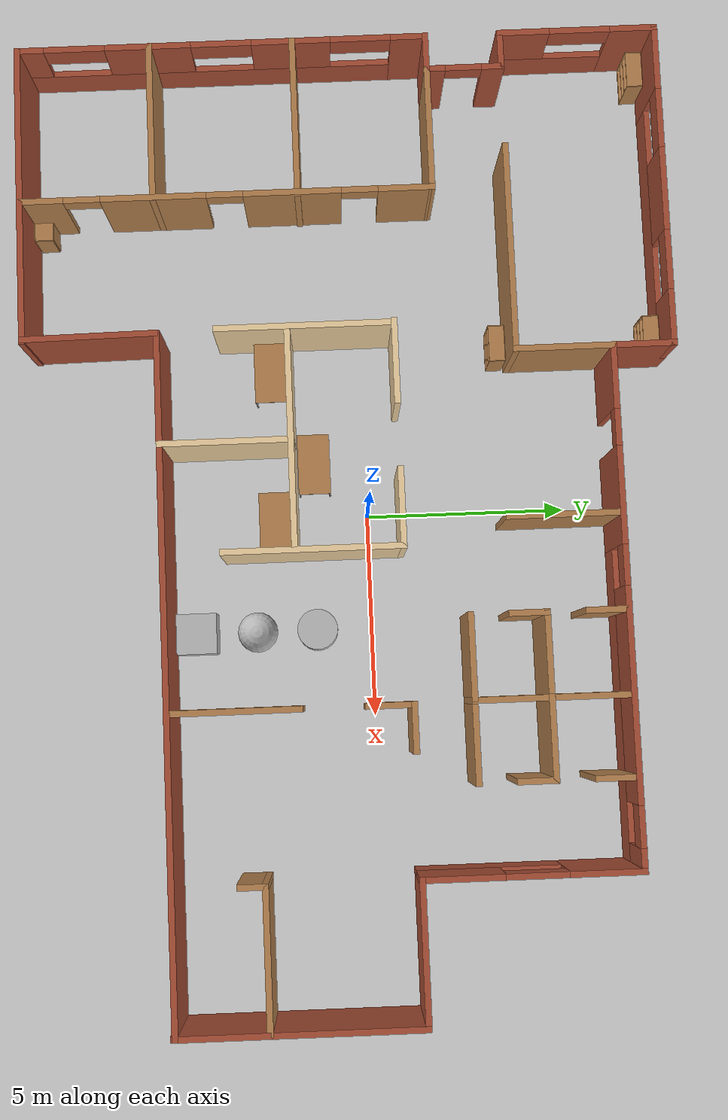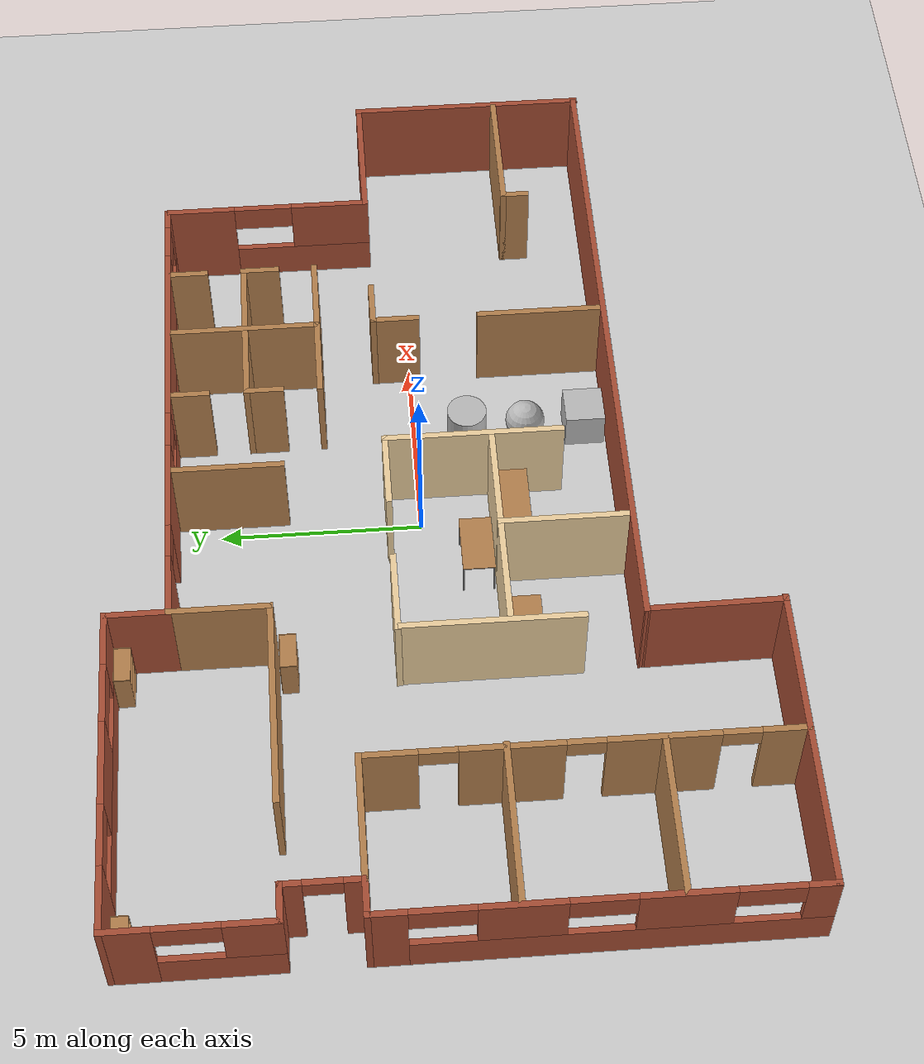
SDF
<sdf version="1.6">
 <world name="default">
  <plugin name="welcome" filename="libwelcome.so"/>
  <light name="sun" type="directional">
   <pose>0 0 10 0 -0 0</pose>
   <diffuse>0.8 0.8 0.8 1</diffuse>
   <specular>0.2 0.2 0.2 1</specular>
   <attenuation>
    <range>1000</range>
    <constant>0.9</constant>
    <linear>0.01</linear>
    <quadratic>0.001</quadratic>
   </attenuation>
   <direction>-0.5 0.1 -0.9</direction>
  </light>
  <model name="ground_plane">
   <static>1</static>
   <link name="link">
    <collision name="collision">
     <geometry><plane><normal>0 0 1</normal><size>100 100</size></plane></geometry>
     <surface>
      <contact><collide_bitmask>65535</collide_bitmask></contact>
      <friction><ode><mu>100</mu><mu2>50</mu2></ode></friction>
     </surface>
    </collision>
    <visual name="visual">
     <cast_shadows>0</cast_shadows>
     <geometry><plane><normal>0 0 1</normal><size>100 100</size></plane></geometry>
     <material>
      <script><uri>file://media/materials/scripts/gazebo.material</uri><name>Gazebo/Grey</name></script>
     </material>
    </visual>
   </link>
  </model>
  <gravity>0 0 -9.8</gravity>
  <magnetic_field>6e-06 2.3e-05 -4.2e-05</magnetic_field>
  <atmosphere type="adiabatic"/>
  <physics name="default_physics" default="0" type="ode">
   <max_step_size>0.001</max_step_size>
   <real_time_factor>1</real_time_factor>
   <real_time_update_rate>1000</real_time_update_rate>
  </physics>
  <scene><ambient>0.4 0.4 0.4 1</ambient><background>0.7 0.7 0.7 1</background><shadows>1</shadows></scene>
  <spherical_coordinates>
   <surface_model>EARTH_WGS84</surface_model>
   <latitude_deg>0</latitude_deg>
   <longitude_deg>0</longitude_deg>
   <elevation>0</elevation>
   <heading_deg>0</heading_deg>
  </spherical_coordinates>
  <model name="MyUdacityOffice">
   <pose>0.26489 -0.33383 0 0 -0 0</pose>
   <link name="Wall_100">
    <collision name="Wall_100_Collision">
     <geometry><box><size>2.089 0.15 2.5</size></box></geometry>
     <pose>0 0 1.25 0 -0 0</pose>
    </collision>
    <visual name="Wall_100_Visual">
     <pose>0 0 1.25 0 -0 0</pose>
     <geometry><box><size>2.089 0.15 2.5</size></box></geometry>
     <material>
      <script><uri>file://media/materials/scripts/gazebo.material</uri><name>Gazebo/Wood</name></script>
      <ambient>0.760784 0.662745 0.627451 1</ambient>
     </material>
     <meta><layer>0</layer></meta>
    </visual>
    <pose>5.4385 2.65847 0 0 -0 0</pose>
   </link>
   <link name="Wall_102">
    <collision name="Wall_102_Collision">
     <geometry><box><size>3.531 0.15 2.5</size></box></geometry>
     <pose>0 0 1.25 0 -0 0</pose>
    </collision>
    <visual name="Wall_102_Visual">
     <pose>0 0 1.25 0 -0 0</pose>
     <geometry><box><size>3.531 0.15 2.5</size></box></geometry>
     <material>
      <script><uri>file://media/materials/scripts/gazebo.material</uri><name>Gazebo/Bricks</name></script>
      <ambient>0.760784 0.662745 0.627451 1</ambient>
     </material>
     <meta><layer>0</layer></meta>
    </visual>
    <pose>10.2845 1.22547 0 0 -0 0</pose>
   </link>
   <link name="Wall_106">
    <collision name="Wall_106_Collision">
     <geometry><box><size>1.637 0.15 2.5</size></box></geometry>
     <pose>0 0 1.25 0 -0 0</pose>
    </collision>
    <visual name="Wall_106_Visual">
     <pose>0 0 1.25 0 -0 0</pose>
     <geometry><box><size>1.637 0.15 2.5</size></box></geometry>
     <material>
      <script><uri>file://media/materials/scripts/gazebo.material</uri><name>Gazebo/Bricks</name></script>
      <ambient>0.760784 0.662745 0.627451 1</ambient>
     </material>
     <meta><layer>0</layer></meta>
    </visual>
    <pose>-3.975 7.18196 0 0 0 -1.5708</pose>
   </link>
   <link name="Wall_108">
    <collision name="Wall_108_Collision">
     <geometry><box><size>2.513 0.15 2.5</size></box></geometry>
     <pose>0 0 1.25 0 -0 0</pose>
    </collision>
    <visual name="Wall_108_Visual">
     <pose>0 0 1.25 0 -0 0</pose>
     <geometry><box><size>2.513 0.15 2.5</size></box></geometry>
     <material>
      <script><uri>file://media/materials/scripts/gazebo.material</uri><name>Gazebo/Wood</name></script>
      <ambient>0.760784 0.662745 0.627451 1</ambient>
     </material>
     <meta><layer>0</layer></meta>
    </visual>
    <pose>-3.975 5.25697 0 0 0 -1.5708</pose>
   </link>
   <link name="Wall_110">
    <collision name="Wall_110_Collision">
     <geometry><box><size>5.25 0.15 2.5</size></box></geometry>
     <pose>0 0 1.25 0 -0 0</pose>
    </collision>
    <visual name="Wall_110_Visual">
     <pose>0 0 1.25 0 -0 0</pose>
     <geometry><box><size>5.25 0.15 2.5</size></box></geometry>
     <material>
      <script><uri>file://media/materials/scripts/gazebo.material</uri><name>Gazebo/Wood</name></script>
      <ambient>0.760784 0.662745 0.627451 1</ambient>
     </material>
     <meta><layer>0</layer></meta>
    </visual>
    <pose>-6.525 4.07547 0 0 -0 3.14159</pose>
   </link>
   <link name="Wall_112">
    <collision name="Wall_112_Collision">
     <geometry><box><size>3.508 0.15 2.5</size></box></geometry>
     <pose>0 0 1.25 0 -0 0</pose>
    </collision>
    <visual name="Wall_112_Visual">
     <pose>0 0 1.25 0 -0 0</pose>
     <geometry><box><size>3.508 0.15 2.5</size></box></geometry>
     <material>
      <script><uri>file://media/materials/scripts/gazebo.material</uri><name>Gazebo/Wood</name></script>
      <ambient>0.760784 0.662745 0.627451 1</ambient>
     </material>
     <meta><layer>0</layer></meta>
    </visual>
    <pose>10.273 -2.44954 0 0 -0 3.14159</pose>
   </link>
   <link name="Wall_115">
    <collision name="Wall_115_Collision">
     <geometry><box><size>0.75 0.15 2.5</size></box></geometry>
     <pose>0 0 1.25 0 -0 0</pose>
    </collision>
    <visual name="Wall_115_Visual">
     <pose>0 0 1.25 0 -0 0</pose>
     <geometry><box><size>0.75 0.15 2.5</size></box></geometry>
     <material>
      <script><uri>file://media/materials/scripts/gazebo.material</uri><name>Gazebo/Wood</name></script>
      <ambient>0.760784 0.662745 0.627451 1</ambient>
     </material>
     <meta><layer>0</layer></meta>
    </visual>
    <pose>8.594 -2.74953 0 0 0 -1.5708</pose>
   </link>
   <link name="Wall_117">
    <collision name="Wall_117_Collision">
     <geometry><box><size>1.25 0.15 2.5</size></box></geometry>
     <pose>0 0 1.25 0 -0 0</pose>
    </collision>
    <visual name="Wall_117_Visual">
     <pose>0 0 1.25 0 -0 0</pose>
     <geometry><box><size>1.25 0.15 2.5</size></box></geometry>
     <material>
      <script><uri>file://media/materials/scripts/gazebo.material</uri><name>Gazebo/Wood</name></script>
      <ambient>0.760784 0.662745 0.627451 1</ambient>
     </material>
     <meta><layer>0</layer></meta>
    </visual>
    <pose>5.055 1.22547 0 0 -0 0</pose>
   </link>
   <link name="Wall_119">
    <collision name="Wall_119_Collision">
     <geometry><box><size>1.25 0.15 2.5</size></box></geometry>
     <pose>0 0 1.25 0 -0 0</pose>
    </collision>
    <visual name="Wall_119_Visual">
     <pose>0 0 1.25 0 -0 0</pose>
     <geometry><box><size>1.25 0.15 2.5</size></box></geometry>
     <material>
      <script><uri>file://media/materials/scripts/gazebo.material</uri><name>Gazebo/Wood</name></script>
      <ambient>0.760784 0.662745 0.627451 1</ambient>
     </material>
     <meta><layer>0</layer></meta>
    </visual>
    <pose>4.505 0.675465 0 0 0 -1.5708</pose>
   </link>
   <link name="Wall_12">
    <pose>-11.975 -2.84953 0 0 0 -1.5708</pose>
    <visual name="Wall_12_Visual_0">
     <pose>-4.67804 0 1.25 0 -0 0</pose>
     <geometry><box><size>0.943917 0.15 2.5</size></box></geometry>
     <material>
      <script><uri>file://media/materials/scripts/gazebo.material</uri><name>Gazebo/Bricks</name></script>
      <ambient>1 1 1 1</ambient>
     </material>
     <meta><layer>0</layer></meta>
    </visual>
    <collision name="Wall_12_Collision_0">
     <geometry><box><size>0.943917 0.15 2.5</size></box></geometry>
     <pose>-4.67804 0 1.25 0 -0 0</pose>
    </collision>
    <visual name="Wall_12_Visual_1">
     <pose>0.471958 0 0.5 0 -0 0</pose>
     <geometry><box><size>9.35608 0.15 1</size></box></geometry>
     <material>
      <script><uri>file://media/materials/scripts/gazebo.material</uri><name>Gazebo/Bricks</name></script>
      <ambient>1 1 1 1</ambient>
     </material>
     <meta><layer>0</layer></meta>
    </visual>
    <collision name="Wall_12_Collision_1">
     <geometry><box><size>9.35608 0.15 1</size></box></geometry>
     <pose>0.471958 0 0.5 0 -0 0</pose>
    </collision>
    <visual name="Wall_12_Visual_2">
     <pose>-1.72352 0 1.75 0 -0 0</pose>
     <geometry><box><size>1.96513 0.15 1.5</size></box></geometry>
     <material>
      <script><uri>file://media/materials/scripts/gazebo.material</uri><name>Gazebo/Bricks</name></script>
      <ambient>1 1 1 1</ambient>
     </material>
     <meta><layer>0</layer></meta>
    </visual>
    <collision name="Wall_12_Collision_2">
     <geometry><box><size>1.96513 0.15 1.5</size></box></geometry>
     <pose>-1.72352 0 1.75 0 -0 0</pose>
    </collision>
    <visual name="Wall_12_Visual_3">
     <pose>1.83263 0 1.75 0 -0 0</pose>
     <geometry><box><size>2.14718 0.15 1.5</size></box></geometry>
     <material>
      <script><uri>file://media/materials/scripts/gazebo.material</uri><name>Gazebo/Bricks</name></script>
      <ambient>1 1 1 1</ambient>
     </material>
     <meta><layer>0</layer></meta>
    </visual>
    <collision name="Wall_12_Collision_3">
     <geometry><box><size>2.14718 0.15 1.5</size></box></geometry>
     <pose>1.83263 0 1.75 0 -0 0</pose>
    </collision>
    <visual name="Wall_12_Visual_4">
     <pose>4.77811 0 1.75 0 -0 0</pose>
     <geometry><box><size>0.743774 0.15 1.5</size></box></geometry>
     <material>
      <script><uri>file://media/materials/scripts/gazebo.material</uri><name>Gazebo/Bricks</name></script>
      <ambient>1 1 1 1</ambient>
     </material>
     <meta><layer>0</layer></meta>
    </visual>
    <collision name="Wall_12_Collision_4">
     <geometry><box><size>0.743774 0.15 1.5</size></box></geometry>
     <pose>4.77811 0 1.75 0 -0 0</pose>
    </collision>
    <visual name="Wall_12_Visual_5">
     <pose>-3.45608 0 2.15 0 -0 0</pose>
     <geometry><box><size>1.5 0.15 0.7</size></box></geometry>
     <material>
      <script><uri>file://media/materials/scripts/gazebo.material</uri><name>Gazebo/Bricks</name></script>
      <ambient>1 1 1 1</ambient>
     </material>
     <meta><layer>0</layer></meta>
    </visual>
    <collision name="Wall_12_Collision_5">
     <geometry><box><size>1.5 0.15 0.7</size></box></geometry>
     <pose>-3.45608 0 2.15 0 -0 0</pose>
    </collision>
    <visual name="Wall_12_Visual_6">
     <pose>0.009042 0 2.15 0 -0 0</pose>
     <geometry><box><size>1.5 0.15 0.7</size></box></geometry>
     <material>
      <script><uri>file://media/materials/scripts/gazebo.material</uri><name>Gazebo/Bricks</name></script>
      <ambient>1 1 1 1</ambient>
     </material>
     <meta><layer>0</layer></meta>
    </visual>
    <collision name="Wall_12_Collision_6">
     <geometry><box><size>1.5 0.15 0.7</size></box></geometry>
     <pose>0.009042 0 2.15 0 -0 0</pose>
    </collision>
    <visual name="Wall_12_Visual_7">
     <pose>3.65623 0 2.15 0 -0 0</pose>
     <geometry><box><size>1.5 0.15 0.7</size></box></geometry>
     <material>
      <script><uri>file://media/materials/scripts/gazebo.material</uri><name>Gazebo/Bricks</name></script>
      <ambient>1 1 1 1</ambient>
     </material>
     <meta><layer>0</layer></meta>
    </visual>
    <collision name="Wall_12_Collision_7">
     <geometry><box><size>1.5 0.15 0.7</size></box></geometry>
     <pose>3.65623 0 2.15 0 -0 0</pose>
    </collision>
   </link>
   <link name="Wall_121">
    <collision name="Wall_121_Collision">
     <geometry><box><size>3.25 0.15 2.5</size></box></geometry>
     <pose>0 0 1.25 0 -0 0</pose>
    </collision>
    <visual name="Wall_121_Visual">
     <pose>0 0 1.25 0 -0 0</pose>
     <geometry><box><size>3.25 0.15 2.5</size></box></geometry>
     <material>
      <script><uri>file://media/materials/scripts/gazebo.material</uri><name>Gazebo/Wood</name></script>
      <ambient>0.760784 0.662745 0.627451 1</ambient>
     </material>
     <meta><layer>0</layer></meta>
    </visual>
    <pose>4.505 -3.04954 0 0 -0 1.5708</pose>
   </link>
   <link name="Wall_125">
    <collision name="Wall_125_Collision">
     <geometry><box><size>4.5 0.15 2.5</size></box></geometry>
     <pose>0 0 1.25 0 -0 0</pose>
    </collision>
    <visual name="Wall_125_Visual">
     <pose>0 0 1.25 0 -0 0</pose>
     <geometry><box><size>4.5 0.15 2.5</size></box></geometry>
     <material>
      <script><uri>file://media/materials/scripts/gazebo.material</uri><name>Gazebo/Grey</name></script>
      <ambient>0.921569 0.807843 0.615686 1</ambient>
     </material>
     <meta><layer>0</layer></meta>
    </visual>
    <pose>-4.75677 -1.03253 0 0 0 -1.5708</pose>
   </link>
   <link name="Wall_129">
    <collision name="Wall_129_Collision">
     <geometry><box><size>2.12236 0.15 2.5</size></box></geometry>
     <pose>0 0 1.25 0 -0 0</pose>
    </collision>
    <visual name="Wall_129_Visual">
     <pose>0 0 1.25 0 -0 0</pose>
     <geometry><box><size>2.12236 0.15 2.5</size></box></geometry>
     <material>
      <script><uri>file://media/materials/scripts/gazebo.material</uri><name>Gazebo/Grey</name></script>
      <ambient>0.921569 0.807843 0.615686 1</ambient>
     </material>
     <meta><layer>0</layer></meta>
    </visual>
    <pose>-3.80118 1.14247 0 0 -0 0</pose>
   </link>
   <link name="Wall_133">
    <collision name="Wall_133_Collision">
     <geometry><box><size>5.39282 0.15 2.5</size></box></geometry>
     <pose>0 0 1.25 0 -0 0</pose>
    </collision>
    <visual name="Wall_133_Visual">
     <pose>0 0 1.25 0 -0 0</pose>
     <geometry><box><size>5.39282 0.15 2.5</size></box></geometry>
     <material>
      <script><uri>file://media/materials/scripts/gazebo.material</uri><name>Gazebo/Grey</name></script>
      <ambient>0.921569 0.807843 0.615686 1</ambient>
     </material>
     <meta><layer>0</layer></meta>
    </visual>
    <pose>-2.04359 -1.47754 0 0 -0 0</pose>
   </link>
   <link name="Wall_136">
    <collision name="Wall_136_Collision">
     <geometry><box><size>3.328 0.15 2.5</size></box></geometry>
     <pose>0 0 1.25 0 -0 0</pose>
    </collision>
    <visual name="Wall_136_Visual">
     <pose>0 0 1.25 0 -0 0</pose>
     <geometry><box><size>3.328 0.15 2.5</size></box></geometry>
     <material>
      <script><uri>file://media/materials/scripts/gazebo.material</uri><name>Gazebo/Grey</name></script>
      <ambient>0.921569 0.807843 0.615686 1</ambient>
     </material>
     <meta><layer>0</layer></meta>
    </visual>
    <pose>-1.971 -3.06654 0 0 0 -1.5708</pose>
   </link>
   <link name="Wall_140">
    <collision name="Wall_140_Collision">
     <geometry><box><size>4.5 0.15 2.5</size></box></geometry>
     <pose>0 0 1.25 0 -0 0</pose>
    </collision>
    <visual name="Wall_140_Visual">
     <pose>0 0 1.25 0 -0 0</pose>
     <geometry><box><size>4.5 0.15 2.5</size></box></geometry>
     <material>
      <script><uri>file://media/materials/scripts/gazebo.material</uri><name>Gazebo/Grey</name></script>
      <ambient>0.921569 0.807843 0.615686 1</ambient>
     </material>
     <meta><layer>0</layer></meta>
    </visual>
    <pose>0.710001 -1.03253 0 0 -0 1.5708</pose>
   </link>
   <link name="Wall_142">
    <collision name="Wall_142_Collision">
     <geometry><box><size>2 0.15 2.5</size></box></geometry>
     <pose>0 0 1.25 0 -0 0</pose>
    </collision>
    <visual name="Wall_142_Visual">
     <pose>0 0 1.25 0 -0 0</pose>
     <geometry><box><size>2 0.15 2.5</size></box></geometry>
     <material>
      <script><uri>file://media/materials/scripts/gazebo.material</uri><name>Gazebo/Grey</name></script>
      <ambient>0.921569 0.807843 0.615686 1</ambient>
     </material>
     <meta><layer>0</layer></meta>
    </visual>
    <pose>-0.215 1.14247 0 0 -0 3.14159</pose>
   </link>
   <link name="Wall_15">
    <pose>-11.125 3.15047 0 0 0 -1.5708</pose>
    <visual name="Wall_15_Visual_0">
     <pose>-0.718002 0 1.25 0 -0 0</pose>
     <geometry><box><size>0.563996 0.15 2.5</size></box></geometry>
     <material>
      <script><uri>file://media/materials/scripts/gazebo.material</uri><name>Gazebo/Bricks</name></script>
      <ambient>0.760784 0.662745 0.627451 1</ambient>
     </material>
     <meta><layer>0</layer></meta>
    </visual>
    <collision name="Wall_15_Collision_0">
     <geometry><box><size>0.563996 0.15 2.5</size></box></geometry>
     <pose>-0.718002 0 1.25 0 -0 0</pose>
    </collision>
    <visual name="Wall_15_Visual_1">
     <pose>0.731998 0 1.25 0 -0 0</pose>
     <geometry><box><size>0.536004 0.15 2.5</size></box></geometry>
     <material>
      <script><uri>file://media/materials/scripts/gazebo.material</uri><name>Gazebo/Bricks</name></script>
      <ambient>0.760784 0.662745 0.627451 1</ambient>
     </material>
     <meta><layer>0</layer></meta>
    </visual>
    <collision name="Wall_15_Collision_1">
     <geometry><box><size>0.536004 0.15 2.5</size></box></geometry>
     <pose>0.731998 0 1.25 0 -0 0</pose>
    </collision>
    <visual name="Wall_15_Visual_2">
     <pose>0.013996 0 2.25 0 -0 0</pose>
     <geometry><box><size>0.9 0.15 0.5</size></box></geometry>
     <material>
      <script><uri>file://media/materials/scripts/gazebo.material</uri><name>Gazebo/Bricks</name></script>
      <ambient>0.760784 0.662745 0.627451 1</ambient>
     </material>
     <meta><layer>0</layer></meta>
    </visual>
    <collision name="Wall_15_Collision_2">
     <geometry><box><size>0.9 0.15 0.5</size></box></geometry>
     <pose>0.013996 0 2.25 0 -0 0</pose>
    </collision>
   </link>
   <link name="Wall_16">
    <collision name="Wall_16_Collision">
     <geometry><box><size>1 0.15 2.5</size></box></geometry>
     <pose>0 0 1.25 0 -0 0</pose>
    </collision>
    <visual name="Wall_16_Visual">
     <pose>0 0 1.25 0 -0 0</pose>
     <geometry><box><size>1 0.15 2.5</size></box></geometry>
     <material>
      <script><uri>file://media/materials/scripts/gazebo.material</uri><name>Gazebo/Bricks</name></script>
      <ambient>0.760784 0.662745 0.627451 1</ambient>
     </material>
     <meta><layer>0</layer></meta>
    </visual>
    <pose>-11.55 2.22546 0 0 -0 3.14159</pose>
   </link>
   <link name="Wall_3">
    <pose>-7.975 7.92546 0 0 -0 0</pose>
    <visual name="Wall_3_Visual_0">
     <pose>-3.24686 0 1.25 0 -0 0</pose>
     <geometry><box><size>1.65628 0.15 2.5</size></box></geometry>
     <material>
      <script><uri>file://media/materials/scripts/gazebo.material</uri><name>Gazebo/Bricks</name></script>
      <ambient>0.760784 0.662745 0.627451 1</ambient>
     </material>
     <meta><layer>0</layer></meta>
    </visual>
    <collision name="Wall_3_Collision_0">
     <geometry><box><size>1.65628 0.15 2.5</size></box></geometry>
     <pose>-3.24686 0 1.25 0 -0 0</pose>
    </collision>
    <visual name="Wall_3_Visual_1">
     <pose>0.828141 0 0.5 0 -0 0</pose>
     <geometry><box><size>6.49372 0.15 1</size></box></geometry>
     <material>
      <script><uri>file://media/materials/scripts/gazebo.material</uri><name>Gazebo/Bricks</name></script>
      <ambient>0.760784 0.662745 0.627451 1</ambient>
     </material>
     <meta><layer>0</layer></meta>
    </visual>
    <collision name="Wall_3_Collision_1">
     <geometry><box><size>6.49372 0.15 1</size></box></geometry>
     <pose>0.828141 0 0.5 0 -0 0</pose>
    </collision>
    <visual name="Wall_3_Visual_2">
     <pose>0.127007 0 1.75 0 -0 0</pose>
     <geometry><box><size>2.09145 0.15 1.5</size></box></geometry>
     <material>
      <script><uri>file://media/materials/scripts/gazebo.material</uri><name>Gazebo/Bricks</name></script>
      <ambient>0.760784 0.662745 0.627451 1</ambient>
     </material>
     <meta><layer>0</layer></meta>
    </visual>
    <collision name="Wall_3_Collision_2">
     <geometry><box><size>2.09145 0.15 1.5</size></box></geometry>
     <pose>0.127007 0 1.75 0 -0 0</pose>
    </collision>
    <visual name="Wall_3_Visual_3">
     <pose>3.37387 0 1.75 0 -0 0</pose>
     <geometry><box><size>1.40227 0.15 1.5</size></box></geometry>
     <material>
      <script><uri>file://media/materials/scripts/gazebo.material</uri><name>Gazebo/Bricks</name></script>
      <ambient>0.760784 0.662745 0.627451 1</ambient>
     </material>
     <meta><layer>0</layer></meta>
    </visual>
    <collision name="Wall_3_Collision_3">
     <geometry><box><size>1.40227 0.15 1.5</size></box></geometry>
     <pose>3.37387 0 1.75 0 -0 0</pose>
    </collision>
    <visual name="Wall_3_Visual_4">
     <pose>-1.66872 0 2.15 0 -0 0</pose>
     <geometry><box><size>1.5 0.15 0.7</size></box></geometry>
     <material>
      <script><uri>file://media/materials/scripts/gazebo.material</uri><name>Gazebo/Bricks</name></script>
      <ambient>0.760784 0.662745 0.627451 1</ambient>
     </material>
     <meta><layer>0</layer></meta>
    </visual>
    <collision name="Wall_3_Collision_4">
     <geometry><box><size>1.5 0.15 0.7</size></box></geometry>
     <pose>-1.66872 0 2.15 0 -0 0</pose>
    </collision>
    <visual name="Wall_3_Visual_5">
     <pose>1.92273 0 2.15 0 -0 0</pose>
     <geometry><box><size>1.5 0.15 0.7</size></box></geometry>
     <material>
      <script><uri>file://media/materials/scripts/gazebo.material</uri><name>Gazebo/Bricks</name></script>
      <ambient>0.760784 0.662745 0.627451 1</ambient>
     </material>
     <meta><layer>0</layer></meta>
    </visual>
    <collision name="Wall_3_Collision_5">
     <geometry><box><size>1.5 0.15 0.7</size></box></geometry>
     <pose>1.92273 0 2.15 0 -0 0</pose>
    </collision>
   </link>
   <link name="Wall_30">
    <collision name="Wall_30_Collision">
     <geometry><box><size>4.05876 0.15 2.5</size></box></geometry>
     <pose>0 0 1.25 0 -0 0</pose>
    </collision>
    <visual name="Wall_30_Visual">
     <pose>0 0 1.25 0 -0 0</pose>
     <geometry><box><size>4.05876 0.15 2.5</size></box></geometry>
     <material>
      <script><uri>file://media/materials/scripts/gazebo.material</uri><name>Gazebo/Wood</name></script>
      <ambient>0.760784 0.662745 0.627451 1</ambient>
     </material>
     <meta><layer>0</layer></meta>
    </visual>
    <pose>-10.0205 -1.09153 0 0 -0 0</pose>
   </link>
   <link name="Wall_34">
    <collision name="Wall_34_Collision">
     <geometry><box><size>4.01576 0.15 2.5</size></box></geometry>
     <pose>0 0 1.25 0 -0 0</pose>
    </collision>
    <visual name="Wall_34_Visual">
     <pose>0 0 1.25 0 -0 0</pose>
     <geometry><box><size>4.01576 0.15 2.5</size></box></geometry>
     <material>
      <script><uri>file://media/materials/scripts/gazebo.material</uri><name>Gazebo/Wood</name></script>
      <ambient>0.760784 0.662745 0.627451 1</ambient>
     </material>
     <meta><layer>0</layer></meta>
    </visual>
    <pose>-10.042 -4.65329 0 0 -0 0</pose>
   </link>
   <link name="Wall_36">
    <collision name="Wall_36_Collision">
     <geometry><box><size>7.5 0.15 2.5</size></box></geometry>
     <pose>0 0 1.25 0 -0 0</pose>
    </collision>
    <visual name="Wall_36_Visual">
     <pose>0 0 1.25 0 -0 0</pose>
     <geometry><box><size>7.5 0.15 2.5</size></box></geometry>
     <material>
      <script><uri>file://media/materials/scripts/gazebo.material</uri><name>Gazebo/Bricks</name></script>
      <ambient>0.760784 0.662745 0.627451 1</ambient>
     </material>
     <meta><layer>0</layer></meta>
    </visual>
    <pose>-8.3 -7.92453 0 0 -0 0</pose>
   </link>
   <link name="Wall_38">
    <pose>-8.111 -2.83103 0 0 -0 1.5704</pose>
    <visual name="Wall_38_Visual_0">
     <pose>-4.57491 0 1.25 0 -0 0</pose>
     <geometry><box><size>1.11318 0.15 2.5</size></box></geometry>
     <material>
      <script><uri>file://media/materials/scripts/gazebo.material</uri><name>Gazebo/Wood</name></script>
      <ambient>0.760784 0.662745 0.627451 1</ambient>
     </material>
     <meta><layer>0</layer></meta>
    </visual>
    <collision name="Wall_38_Collision_0">
     <geometry><box><size>1.11318 0.15 2.5</size></box></geometry>
     <pose>-4.57491 0 1.25 0 -0 0</pose>
    </collision>
    <visual name="Wall_38_Visual_1">
     <pose>-1.81271 0 1.25 0 -0 0</pose>
     <geometry><box><size>2.6112 0.15 2.5</size></box></geometry>
     <material>
      <script><uri>file://media/materials/scripts/gazebo.material</uri><name>Gazebo/Wood</name></script>
      <ambient>0.760784 0.662745 0.627451 1</ambient>
     </material>
     <meta><layer>0</layer></meta>
    </visual>
    <collision name="Wall_38_Collision_1">
     <geometry><box><size>2.6112 0.15 2.5</size></box></geometry>
     <pose>-1.81271 0 1.25 0 -0 0</pose>
    </collision>
    <visual name="Wall_38_Visual_2">
     <pose>1.60633 0 1.25 0 -0 0</pose>
     <geometry><box><size>2.42689 0.15 2.5</size></box></geometry>
     <material>
      <script><uri>file://media/materials/scripts/gazebo.material</uri><name>Gazebo/Wood</name></script>
      <ambient>0.760784 0.662745 0.627451 1</ambient>
     </material>
     <meta><layer>0</layer></meta>
    </visual>
    <collision name="Wall_38_Collision_2">
     <geometry><box><size>2.42689 0.15 2.5</size></box></geometry>
     <pose>1.60633 0 1.25 0 -0 0</pose>
    </collision>
    <visual name="Wall_38_Visual_3">
     <pose>4.42564 0 1.25 0 -0 0</pose>
     <geometry><box><size>1.41172 0.15 2.5</size></box></geometry>
     <material>
      <script><uri>file://media/materials/scripts/gazebo.material</uri><name>Gazebo/Wood</name></script>
      <ambient>0.760784 0.662745 0.627451 1</ambient>
     </material>
     <meta><layer>0</layer></meta>
    </visual>
    <collision name="Wall_38_Collision_3">
     <geometry><box><size>1.41172 0.15 2.5</size></box></geometry>
     <pose>4.42564 0 1.25 0 -0 0</pose>
    </collision>
    <visual name="Wall_38_Visual_4">
     <pose>-3.56832 0 2.25 0 -0 0</pose>
     <geometry><box><size>0.9 0.15 0.5</size></box></geometry>
     <material>
      <script><uri>file://media/materials/scripts/gazebo.material</uri><name>Gazebo/Wood</name></script>
      <ambient>0.760784 0.662745 0.627451 1</ambient>
     </material>
     <meta><layer>0</layer></meta>
    </visual>
    <collision name="Wall_38_Collision_4">
     <geometry><box><size>0.9 0.15 0.5</size></box></geometry>
     <pose>-3.56832 0 2.25 0 -0 0</pose>
    </collision>
    <visual name="Wall_38_Visual_5">
     <pose>-0.057112 0 2.25 0 -0 0</pose>
     <geometry><box><size>0.9 0.15 0.5</size></box></geometry>
     <material>
      <script><uri>file://media/materials/scripts/gazebo.material</uri><name>Gazebo/Wood</name></script>
      <ambient>0.760784 0.662745 0.627451 1</ambient>
     </material>
     <meta><layer>0</layer></meta>
    </visual>
    <collision name="Wall_38_Collision_5">
     <geometry><box><size>0.9 0.15 0.5</size></box></geometry>
     <pose>-0.057112 0 2.25 0 -0 0</pose>
    </collision>
    <visual name="Wall_38_Visual_6">
     <pose>3.26978 0 2.25 0 -0 0</pose>
     <geometry><box><size>0.9 0.15 0.5</size></box></geometry>
     <material>
      <script><uri>file://media/materials/scripts/gazebo.material</uri><name>Gazebo/Wood</name></script>
      <ambient>0.760784 0.662745 0.627451 1</ambient>
     </material>
     <meta><layer>0</layer></meta>
    </visual>
    <collision name="Wall_38_Collision_6">
     <geometry><box><size>0.9 0.15 0.5</size></box></geometry>
     <pose>3.26978 0 2.25 0 -0 0</pose>
    </collision>
   </link>
   <link name="Wall_40">
    <collision name="Wall_40_Collision">
     <geometry><box><size>3.166 0.15 2.5</size></box></geometry>
     <pose>0 0 1.25 0 -0 0</pose>
    </collision>
    <visual name="Wall_40_Visual">
     <pose>0 0 1.25 0 -0 0</pose>
     <geometry><box><size>3.166 0.15 2.5</size></box></geometry>
     <material>
      <script><uri>file://media/materials/scripts/gazebo.material</uri><name>Gazebo/Wood</name></script>
      <ambient>0.760784 0.662745 0.627451 1</ambient>
     </material>
     <meta><layer>0</layer></meta>
    </visual>
    <pose>-9.617 2.22546 0 0 -0 3.14159</pose>
   </link>
   <link name="Wall_47">
    <pose>2.3095 6.43846 0 0 -0 0</pose>
    <visual name="Wall_47_Visual_0">
     <pose>-5.53815 0 1.25 0 -0 0</pose>
     <geometry><box><size>1.64269 0.15 2.5</size></box></geometry>
     <material>
      <script><uri>file://media/materials/scripts/gazebo.material</uri><name>Gazebo/Bricks</name></script>
      <ambient>0.760784 0.662745 0.627451 1</ambient>
     </material>
     <meta><layer>0</layer></meta>
    </visual>
    <collision name="Wall_47_Collision_0">
     <geometry><box><size>1.64269 0.15 2.5</size></box></geometry>
     <pose>-5.53815 0 1.25 0 -0 0</pose>
    </collision>
    <visual name="Wall_47_Visual_1">
     <pose>-2.61941 0 1.25 0 -0 0</pose>
     <geometry><box><size>2.3948 0.15 2.5</size></box></geometry>
     <material>
      <script><uri>file://media/materials/scripts/gazebo.material</uri><name>Gazebo/Bricks</name></script>
      <ambient>0.760784 0.662745 0.627451 1</ambient>
     </material>
     <meta><layer>0</layer></meta>
    </visual>
    <collision name="Wall_47_Collision_1">
     <geometry><box><size>2.3948 0.15 2.5</size></box></geometry>
     <pose>-2.61941 0 1.25 0 -0 0</pose>
    </collision>
    <visual name="Wall_47_Visual_2">
     <pose>2.46875 0 0.5 0 -0 0</pose>
     <geometry><box><size>7.78151 0.15 1</size></box></geometry>
     <material>
      <script><uri>file://media/materials/scripts/gazebo.material</uri><name>Gazebo/Bricks</name></script>
      <ambient>0.760784 0.662745 0.627451 1</ambient>
     </material>
     <meta><layer>0</layer></meta>
    </visual>
    <collision name="Wall_47_Collision_2">
     <geometry><box><size>7.78151 0.15 1</size></box></geometry>
     <pose>2.46875 0 0.5 0 -0 0</pose>
    </collision>
    <visual name="Wall_47_Visual_3">
     <pose>2.16693 0 1.75 0 -0 0</pose>
     <geometry><box><size>5.17786 0.15 1.5</size></box></geometry>
     <material>
      <script><uri>file://media/materials/scripts/gazebo.material</uri><name>Gazebo/Bricks</name></script>
      <ambient>0.760784 0.662745 0.627451 1</ambient>
     </material>
     <meta><layer>0</layer></meta>
    </visual>
    <collision name="Wall_47_Collision_3">
     <geometry><box><size>5.17786 0.15 1.5</size></box></geometry>
     <pose>2.16693 0 1.75 0 -0 0</pose>
    </collision>
    <visual name="Wall_47_Visual_4">
     <pose>6.05768 0 1.75 0 -0 0</pose>
     <geometry><box><size>0.603641 0.15 1.5</size></box></geometry>
     <material>
      <script><uri>file://media/materials/scripts/gazebo.material</uri><name>Gazebo/Bricks</name></script>
      <ambient>0.760784 0.662745 0.627451 1</ambient>
     </material>
     <meta><layer>0</layer></meta>
    </visual>
    <collision name="Wall_47_Collision_4">
     <geometry><box><size>0.603641 0.15 1.5</size></box></geometry>
     <pose>6.05768 0 1.75 0 -0 0</pose>
    </collision>
    <visual name="Wall_47_Visual_5">
     <pose>-0.922005 0 2.15 0 -0 0</pose>
     <geometry><box><size>1 0.15 0.7</size></box></geometry>
     <material>
      <script><uri>file://media/materials/scripts/gazebo.material</uri><name>Gazebo/Bricks</name></script>
      <ambient>0.760784 0.662745 0.627451 1</ambient>
     </material>
     <meta><layer>0</layer></meta>
    </visual>
    <collision name="Wall_47_Collision_5">
     <geometry><box><size>1 0.15 0.7</size></box></geometry>
     <pose>-0.922005 0 2.15 0 -0 0</pose>
    </collision>
    <visual name="Wall_47_Visual_6">
     <pose>5.25586 0 2.15 0 -0 0</pose>
     <geometry><box><size>1 0.15 0.7</size></box></geometry>
     <material>
      <script><uri>file://media/materials/scripts/gazebo.material</uri><name>Gazebo/Bricks</name></script>
      <ambient>0.760784 0.662745 0.627451 1</ambient>
     </material>
     <meta><layer>0</layer></meta>
    </visual>
    <collision name="Wall_47_Collision_6">
     <geometry><box><size>1 0.15 0.7</size></box></geometry>
     <pose>5.25586 0 2.15 0 -0 0</pose>
    </collision>
    <visual name="Wall_47_Visual_7">
     <pose>-4.26681 0 2.25 0 -0 0</pose>
     <geometry><box><size>0.9 0.15 0.5</size></box></geometry>
     <material>
      <script><uri>file://media/materials/scripts/gazebo.material</uri><name>Gazebo/Bricks</name></script>
      <ambient>0.760784 0.662745 0.627451 1</ambient>
     </material>
     <meta><layer>0</layer></meta>
    </visual>
    <collision name="Wall_47_Collision_7">
     <geometry><box><size>0.9 0.15 0.5</size></box></geometry>
     <pose>-4.26681 0 2.25 0 -0 0</pose>
    </collision>
   </link>
   <link name="Wall_49">
    <pose>8.594 3.83196 0 0 0 -1.5708</pose>
    <visual name="Wall_49_Visual_0">
     <pose>-1.76457 0 1.25 0 -0 0</pose>
     <geometry><box><size>1.83486 0.15 2.5</size></box></geometry>
     <material>
      <script><uri>file://media/materials/scripts/gazebo.material</uri><name>Gazebo/Bricks</name></script>
      <ambient>0.760784 0.662745 0.627451 1</ambient>
     </material>
     <meta><layer>0</layer></meta>
    </visual>
    <collision name="Wall_49_Collision_0">
     <geometry><box><size>1.83486 0.15 2.5</size></box></geometry>
     <pose>-1.76457 0 1.25 0 -0 0</pose>
    </collision>
    <visual name="Wall_49_Visual_1">
     <pose>0.91743 0 0.5 0 -0 0</pose>
     <geometry><box><size>3.52913 0.15 1</size></box></geometry>
     <material>
      <script><uri>file://media/materials/scripts/gazebo.material</uri><name>Gazebo/Bricks</name></script>
      <ambient>0.760784 0.662745 0.627451 1</ambient>
     </material>
     <meta><layer>0</layer></meta>
    </visual>
    <collision name="Wall_49_Collision_1">
     <geometry><box><size>3.52913 0.15 1</size></box></geometry>
     <pose>0.91743 0 0.5 0 -0 0</pose>
    </collision>
    <visual name="Wall_49_Visual_2">
     <pose>1.66743 0 1.75 0 -0 0</pose>
     <geometry><box><size>2.02913 0.15 1.5</size></box></geometry>
     <material>
      <script><uri>file://media/materials/scripts/gazebo.material</uri><name>Gazebo/Bricks</name></script>
      <ambient>0.760784 0.662745 0.627451 1</ambient>
     </material>
     <meta><layer>0</layer></meta>
    </visual>
    <collision name="Wall_49_Collision_2">
     <geometry><box><size>2.02913 0.15 1.5</size></box></geometry>
     <pose>1.66743 0 1.75 0 -0 0</pose>
    </collision>
    <visual name="Wall_49_Visual_3">
     <pose>-0.097136 0 2.15 0 -0 0</pose>
     <geometry><box><size>1.5 0.15 0.7</size></box></geometry>
     <material>
      <script><uri>file://media/materials/scripts/gazebo.material</uri><name>Gazebo/Bricks</name></script>
      <ambient>0.760784 0.662745 0.627451 1</ambient>
     </material>
     <meta><layer>0</layer></meta>
    </visual>
    <collision name="Wall_49_Collision_3">
     <geometry><box><size>1.5 0.15 0.7</size></box></geometry>
     <pose>-0.097136 0 2.15 0 -0 0</pose>
    </collision>
   </link>
   <link name="Wall_5">
    <pose>-11.975 6.00047 0 0 0 -1.5708</pose>
    <visual name="Wall_5_Visual_0">
     <pose>-1.40991 0 1.25 0 -0 0</pose>
     <geometry><box><size>1.18019 0.15 2.5</size></box></geometry>
     <material>
      <script><uri>file://media/materials/scripts/gazebo.material</uri><name>Gazebo/Bricks</name></script>
      <ambient>0.760784 0.662745 0.627451 1</ambient>
     </material>
     <meta><layer>0</layer></meta>
    </visual>
    <collision name="Wall_5_Collision_0">
     <geometry><box><size>1.18019 0.15 2.5</size></box></geometry>
     <pose>-1.40991 0 1.25 0 -0 0</pose>
    </collision>
    <visual name="Wall_5_Visual_1">
     <pose>0.590093 0 0.5 0 -0 0</pose>
     <geometry><box><size>2.81981 0.15 1</size></box></geometry>
     <material>
      <script><uri>file://media/materials/scripts/gazebo.material</uri><name>Gazebo/Bricks</name></script>
      <ambient>0.760784 0.662745 0.627451 1</ambient>
     </material>
     <meta><layer>0</layer></meta>
    </visual>
    <collision name="Wall_5_Collision_1">
     <geometry><box><size>2.81981 0.15 1</size></box></geometry>
     <pose>0.590093 0 0.5 0 -0 0</pose>
    </collision>
    <visual name="Wall_5_Visual_2">
     <pose>1.34009 0 1.75 0 -0 0</pose>
     <geometry><box><size>1.31981 0.15 1.5</size></box></geometry>
     <material>
      <script><uri>file://media/materials/scripts/gazebo.material</uri><name>Gazebo/Bricks</name></script>
      <ambient>0.760784 0.662745 0.627451 1</ambient>
     </material>
     <meta><layer>0</layer></meta>
    </visual>
    <collision name="Wall_5_Collision_2">
     <geometry><box><size>1.31981 0.15 1.5</size></box></geometry>
     <pose>1.34009 0 1.75 0 -0 0</pose>
    </collision>
    <visual name="Wall_5_Visual_3">
     <pose>-0.069814 0 2.15 0 -0 0</pose>
     <geometry><box><size>1.5 0.15 0.7</size></box></geometry>
     <material>
      <script><uri>file://media/materials/scripts/gazebo.material</uri><name>Gazebo/Bricks</name></script>
      <ambient>0.760784 0.662745 0.627451 1</ambient>
     </material>
     <meta><layer>0</layer></meta>
    </visual>
    <collision name="Wall_5_Collision_3">
     <geometry><box><size>1.5 0.15 0.7</size></box></geometry>
     <pose>-0.069814 0 2.15 0 -0 0</pose>
    </collision>
   </link>
   <link name="Wall_52">
    <collision name="Wall_52_Collision">
     <geometry><box><size>6.06118 0.15 2.5</size></box></geometry>
     <pose>0 0 1.25 0 -0 0</pose>
    </collision>
    <visual name="Wall_52_Visual">
     <pose>0 0 1.25 0 -0 0</pose>
     <geometry><box><size>6.06118 0.15 2.5</size></box></geometry>
     <material>
      <script><uri>file://media/materials/scripts/gazebo.material</uri><name>Gazebo/Bricks</name></script>
      <ambient>0.760784 0.662745 0.627451 1</ambient>
     </material>
     <meta><layer>0</layer></meta>
    </visual>
    <pose>11.975 -1.73012 0 0 0 -1.5708</pose>
   </link>
   <link name="Wall_53">
    <collision name="Wall_53_Collision">
     <geometry><box><size>16.8309 0.15 2.5</size></box></geometry>
     <pose>0 0 1.25 0 -0 0</pose>
    </collision>
    <visual name="Wall_53_Visual">
     <pose>0 0 1.25 0 -0 0</pose>
     <geometry><box><size>16.8309 0.15 2.5</size></box></geometry>
     <material>
      <script><uri>file://media/materials/scripts/gazebo.material</uri><name>Gazebo/Bricks</name></script>
      <ambient>0.760784 0.662745 0.627451 1</ambient>
     </material>
     <meta><layer>0</layer></meta>
    </visual>
    <pose>3.63455 -4.65512 0 0 -0 3.14159</pose>
   </link>
   <link name="Wall_54">
    <collision name="Wall_54_Collision">
     <geometry><box><size>3.38907 0.15 2.5</size></box></geometry>
     <pose>0 0 1.25 0 -0 0</pose>
    </collision>
    <visual name="Wall_54_Visual">
     <pose>0 0 1.25 0 -0 0</pose>
     <geometry><box><size>3.38907 0.15 2.5</size></box></geometry>
     <material>
      <script><uri>file://media/materials/scripts/gazebo.material</uri><name>Gazebo/Bricks</name></script>
      <ambient>0.760784 0.662745 0.627451 1</ambient>
     </material>
     <meta><layer>0</layer></meta>
    </visual>
    <pose>-4.68568 -6.30513 0 0 0 -1.55831</pose>
   </link>
   <link name="Wall_56">
    <collision name="Wall_56_Collision">
     <geometry><box><size>2.75 0.15 2.5</size></box></geometry>
     <pose>0 0 1.25 0 -0 0</pose>
    </collision>
    <visual name="Wall_56_Visual">
     <pose>0 0 1.25 0 -0 0</pose>
     <geometry><box><size>2.75 0.15 2.5</size></box></geometry>
     <material>
      <script><uri>file://media/materials/scripts/gazebo.material</uri><name>Gazebo/Wood</name></script>
      <ambient>0.760784 0.662745 0.627451 1</ambient>
     </material>
     <meta><layer>0</layer></meta>
    </visual>
    <pose>0.113999 4.98787 0 0 0 -1.5708</pose>
   </link>
   <link name="Wall_58">
    <collision name="Wall_58_Collision">
     <geometry><box><size>1 0.15 2.5</size></box></geometry>
     <pose>0 0 1.25 0 -0 0</pose>
    </collision>
    <visual name="Wall_58_Visual">
     <pose>0 0 1.25 0 -0 0</pose>
     <geometry><box><size>1 0.15 2.5</size></box></geometry>
     <material>
      <script><uri>file://media/materials/scripts/gazebo.material</uri><name>Gazebo/Wood</name></script>
      <ambient>0.760784 0.662745 0.627451 1</ambient>
     </material>
     <meta><layer>0</layer></meta>
    </visual>
    <pose>2.44 5.90046 0 0 0 -1.5708</pose>
   </link>
   <link name="Wall_62">
    <collision name="Wall_62_Collision">
     <geometry><box><size>1 0.15 2.5</size></box></geometry>
     <pose>0 0 1.25 0 -0 0</pose>
    </collision>
    <visual name="Wall_62_Visual">
     <pose>0 0 1.25 0 -0 0</pose>
     <geometry><box><size>1 0.15 2.5</size></box></geometry>
     <material>
      <script><uri>file://media/materials/scripts/gazebo.material</uri><name>Gazebo/Wood</name></script>
      <ambient>0.760784 0.662745 0.627451 1</ambient>
     </material>
     <meta><layer>0</layer></meta>
    </visual>
    <pose>6.408 5.90046 0 0 0 -1.5708</pose>
   </link>
   <link name="Wall_68">
    <collision name="Wall_68_Collision">
     <geometry><box><size>3.8 0.15 2.5</size></box></geometry>
     <pose>0 0 1.25 0 -0 0</pose>
    </collision>
    <visual name="Wall_68_Visual">
     <pose>0 0 1.25 0 -0 0</pose>
     <geometry><box><size>3.8 0.15 2.5</size></box></geometry>
     <material>
      <script><uri>file://media/materials/scripts/gazebo.material</uri><name>Gazebo/Wood</name></script>
      <ambient>0.760784 0.662745 0.627451 1</ambient>
     </material>
     <meta><layer>0</layer></meta>
    </visual>
    <pose>4.469 4.48346 0 0 0 -1.5708</pose>
   </link>
   <link name="Wall_7">
    <collision name="Wall_7_Collision">
     <geometry><box><size>1 0.15 2.5</size></box></geometry>
     <pose>0 0 1.25 0 -0 0</pose>
    </collision>
    <visual name="Wall_7_Visual">
     <pose>0 0 1.25 0 -0 0</pose>
     <geometry><box><size>1 0.15 2.5</size></box></geometry>
     <material>
      <script><uri>file://media/materials/scripts/gazebo.material</uri><name>Gazebo/Bricks</name></script>
      <ambient>0.760784 0.662745 0.627451 1</ambient>
     </material>
     <meta><layer>0</layer></meta>
    </visual>
    <pose>-11.55 4.07547 0 0 -0 0</pose>
   </link>
   <link name="Wall_8">
    <collision name="Wall_8_Collision">
     <geometry><box><size>0.15 0.15 2.5</size></box></geometry>
     <pose>0 0 1.25 0 -0 0</pose>
    </collision>
    <visual name="Wall_8_Visual">
     <pose>0 0 1.25 0 -0 0</pose>
     <geometry><box><size>0.15 0.15 2.5</size></box></geometry>
     <material>
      <script><uri>file://media/materials/scripts/gazebo.material</uri><name>Gazebo/Bricks</name></script>
      <ambient>0.760784 0.662745 0.627451 1</ambient>
     </material>
     <meta><layer>0</layer></meta>
    </visual>
    <pose>-11.125 4.07547 0 0 -0 0</pose>
   </link>
   <link name="Wall_86">
    <collision name="Wall_86_Collision">
     <geometry><box><size>2.166 0.15 2.5</size></box></geometry>
     <pose>0 0 1.25 0 -0 0</pose>
    </collision>
    <visual name="Wall_86_Visual">
     <pose>0 0 1.25 0 -0 0</pose>
     <geometry><box><size>2.166 0.15 2.5</size></box></geometry>
     <material>
      <script><uri>file://media/materials/scripts/gazebo.material</uri><name>Gazebo/Wood</name></script>
      <ambient>0.760784 0.662745 0.627451 1</ambient>
     </material>
     <meta><layer>0</layer></meta>
    </visual>
    <pose>3.448 4.48546 0 0 -0 3.14159</pose>
   </link>
   <link name="Wall_88">
    <collision name="Wall_88_Collision">
     <geometry><box><size>2.102 0.15 2.5</size></box></geometry>
     <pose>0 0 1.25 0 -0 0</pose>
    </collision>
    <visual name="Wall_88_Visual">
     <pose>0 0 1.25 0 -0 0</pose>
     <geometry><box><size>2.102 0.15 2.5</size></box></geometry>
     <material>
      <script><uri>file://media/materials/scripts/gazebo.material</uri><name>Gazebo/Wood</name></script>
      <ambient>0.760784 0.662745 0.627451 1</ambient>
     </material>
     <meta><layer>0</layer></meta>
    </visual>
    <pose>5.432 4.48546 0 0 -0 0</pose>
   </link>
   <link name="Wall_94">
    <collision name="Wall_94_Collision">
     <geometry><box><size>1 0.15 2.5</size></box></geometry>
     <pose>0 0 1.25 0 -0 0</pose>
    </collision>
    <visual name="Wall_94_Visual">
     <pose>0 0 1.25 0 -0 0</pose>
     <geometry><box><size>1 0.15 2.5</size></box></geometry>
     <material>
      <script><uri>file://media/materials/scripts/gazebo.material</uri><name>Gazebo/Wood</name></script>
      <ambient>0.760784 0.662745 0.627451 1</ambient>
     </material>
     <meta><layer>0</layer></meta>
    </visual>
    <pose>2.44 4.06046 0 0 0 -1.5708</pose>
   </link>
   <link name="Wall_96">
    <collision name="Wall_96_Collision">
     <geometry><box><size>1 0.15 2.5</size></box></geometry>
     <pose>0 0 1.25 0 -0 0</pose>
    </collision>
    <visual name="Wall_96_Visual">
     <pose>0 0 1.25 0 -0 0</pose>
     <geometry><box><size>1 0.15 2.5</size></box></geometry>
     <material>
      <script><uri>file://media/materials/scripts/gazebo.material</uri><name>Gazebo/Wood</name></script>
      <ambient>0.760784 0.662745 0.627451 1</ambient>
     </material>
     <meta><layer>0</layer></meta>
    </visual>
    <pose>6.408 4.06046 0 0 0 -1.5708</pose>
   </link>
   <link name="Wall_98">
    <collision name="Wall_98_Collision">
     <geometry><box><size>2.179 0.15 2.5</size></box></geometry>
     <pose>0 0 1.25 0 -0 0</pose>
    </collision>
    <visual name="Wall_98_Visual">
     <pose>0 0 1.25 0 -0 0</pose>
     <geometry><box><size>2.179 0.15 2.5</size></box></geometry>
     <material>
      <script><uri>file://media/materials/scripts/gazebo.material</uri><name>Gazebo/Wood</name></script>
      <ambient>0.760784 0.662745 0.627451 1</ambient>
     </material>
     <meta><layer>0</layer></meta>
    </visual>
    <pose>3.4545 2.65847 0 0 -0 3.14159</pose>
   </link>
   <static>1</static>
  </model>
  <model name="bookshelf">
   <static>1</static>
   <link name="link">
    <inertial><mass>1</mass></inertial>
    <collision name="back">
     <pose>0 0.005 0.6 0 -0 0</pose>
     <geometry><box><size>0.9 0.01 1.2</size></box></geometry>
    </collision>
    <visual name="visual1">
     <pose>0 0.005 0.6 0 -0 0</pose>
     <geometry><box><size>0.9 0.01 1.2</size></box></geometry>
     <material>
      <script><uri>file://media/materials/scripts/gazebo.material</uri><name>Gazebo/Wood</name></script>
     </material>
    </visual>
    <collision name="left_side">
     <pose>0.45 -0.195 0.6 0 -0 0</pose>
     <geometry><box><size>0.02 0.4 1.2</size></box></geometry>
    </collision>
    <visual name="visual2">
     <pose>0.45 -0.195 0.6 0 -0 0</pose>
     <geometry><box><size>0.02 0.4 1.2</size></box></geometry>
     <material>
      <script><uri>file://media/materials/scripts/gazebo.material</uri><name>Gazebo/Wood</name></script>
     </material>
    </visual>
    <collision name="right_side">
     <pose>-0.45 -0.195 0.6 0 -0 0</pose>
     <geometry><box><size>0.02 0.4 1.2</size></box></geometry>
    </collision>
    <visual name="visual3">
     <pose>-0.45 -0.195 0.6 0 -0 0</pose>
     <geometry><box><size>0.02 0.4 1.2</size></box></geometry>
     <material>
      <script><uri>file://media/materials/scripts/gazebo.material</uri><name>Gazebo/Wood</name></script>
     </material>
    </visual>
    <collision name="bottom">
     <pose>0 -0.195 0.03 0 -0 0</pose>
     <geometry><box><size>0.88 0.4 0.06</size></box></geometry>
    </collision>
    <visual name="visual4">
     <pose>0 -0.195 0.03 0 -0 0</pose>
     <geometry><box><size>0.88 0.4 0.06</size></box></geometry>
     <material>
      <script><uri>file://media/materials/scripts/gazebo.material</uri><name>Gazebo/Wood</name></script>
     </material>
    </visual>
    <collision name="top">
     <pose>0 -0.195 1.19 0 -0 0</pose>
     <geometry><box><size>0.88 0.4 0.02</size></box></geometry>
    </collision>
    <visual name="visual5">
     <pose>0 -0.195 1.19 0 -0 0</pose>
     <geometry><box><size>0.88 0.4 0.02</size></box></geometry>
     <material>
      <script><uri>file://media/materials/scripts/gazebo.material</uri><name>Gazebo/Wood</name></script>
     </material>
    </visual>
    <collision name="low_shelf">
     <pose>0 -0.195 0.43 0 -0 0</pose>
     <geometry><box><size>0.88 0.4 0.02</size></box></geometry>
    </collision>
    <visual name="visual6">
     <pose>0 -0.195 0.43 0 -0 0</pose>
     <geometry><box><size>0.88 0.4 0.02</size></box></geometry>
     <material>
      <script><uri>file://media/materials/scripts/gazebo.material</uri><name>Gazebo/Wood</name></script>
     </material>
    </visual>
    <collision name="high_shelf">
     <pose>0 -0.195 0.8 0 -0 0</pose>
     <geometry><box><size>0.88 0.4 0.02</size></box></geometry>
    </collision>
    <visual name="visual7">
     <pose>0 -0.195 0.8 0 -0 0</pose>
     <geometry><box><size>0.88 0.4 0.02</size></box></geometry>
     <material>
      <script><uri>file://media/materials/scripts/gazebo.material</uri><name>Gazebo/Wood</name></script>
     </material>
    </visual>
   </link>
   <pose>-11.1705 7.48953 0 0 -0 0</pose>
  </model>
  <model name="bookshelf_0">
   <static>1</static>
   <link name="link">
    <inertial><mass>1</mass></inertial>
    <collision name="back">
     <pose>0 0.005 0.6 0 -0 0</pose>
     <geometry><box><size>0.9 0.01 1.2</size></box></geometry>
    </collision>
    <visual name="visual1">
     <pose>0 0.005 0.6 0 -0 0</pose>
     <geometry><box><size>0.9 0.01 1.2</size></box></geometry>
     <material>
      <script><uri>file://media/materials/scripts/gazebo.material</uri><name>Gazebo/Wood</name></script>
     </material>
    </visual>
    <collision name="left_side">
     <pose>0.45 -0.195 0.6 0 -0 0</pose>
     <geometry><box><size>0.02 0.4 1.2</size></box></geometry>
    </collision>
    <visual name="visual2">
     <pose>0.45 -0.195 0.6 0 -0 0</pose>
     <geometry><box><size>0.02 0.4 1.2</size></box></geometry>
     <material>
      <script><uri>file://media/materials/scripts/gazebo.material</uri><name>Gazebo/Wood</name></script>
     </material>
    </visual>
    <collision name="right_side">
     <pose>-0.45 -0.195 0.6 0 -0 0</pose>
     <geometry><box><size>0.02 0.4 1.2</size></box></geometry>
    </collision>
    <visual name="visual3">
     <pose>-0.45 -0.195 0.6 0 -0 0</pose>
     <geometry><box><size>0.02 0.4 1.2</size></box></geometry>
     <material>
      <script><uri>file://media/materials/scripts/gazebo.material</uri><name>Gazebo/Wood</name></script>
     </material>
    </visual>
    <collision name="bottom">
     <pose>0 -0.195 0.03 0 -0 0</pose>
     <geometry><box><size>0.88 0.4 0.06</size></box></geometry>
    </collision>
    <visual name="visual4">
     <pose>0 -0.195 0.03 0 -0 0</pose>
     <geometry><box><size>0.88 0.4 0.06</size></box></geometry>
     <material>
      <script><uri>file://media/materials/scripts/gazebo.material</uri><name>Gazebo/Wood</name></script>
     </material>
    </visual>
    <collision name="top">
     <pose>0 -0.195 1.19 0 -0 0</pose>
     <geometry><box><size>0.88 0.4 0.02</size></box></geometry>
    </collision>
    <visual name="visual5">
     <pose>0 -0.195 1.19 0 -0 0</pose>
     <geometry><box><size>0.88 0.4 0.02</size></box></geometry>
     <material>
      <script><uri>file://media/materials/scripts/gazebo.material</uri><name>Gazebo/Wood</name></script>
     </material>
    </visual>
    <collision name="low_shelf">
     <pose>0 -0.195 0.43 0 -0 0</pose>
     <geometry><box><size>0.88 0.4 0.02</size></box></geometry>
    </collision>
    <visual name="visual6">
     <pose>0 -0.195 0.43 0 -0 0</pose>
     <geometry><box><size>0.88 0.4 0.02</size></box></geometry>
     <material>
      <script><uri>file://media/materials/scripts/gazebo.material</uri><name>Gazebo/Wood</name></script>
     </material>
    </visual>
    <collision name="high_shelf">
     <pose>0 -0.195 0.8 0 -0 0</pose>
     <geometry><box><size>0.88 0.4 0.02</size></box></geometry>
    </collision>
    <visual name="visual7">
     <pose>0 -0.195 0.8 0 -0 0</pose>
     <geometry><box><size>0.88 0.4 0.02</size></box></geometry>
     <material>
      <script><uri>file://media/materials/scripts/gazebo.material</uri><name>Gazebo/Wood</name></script>
     </material>
    </visual>
   </link>
   <pose>-4.1534 3.60671 0 0 -0 0</pose>
  </model>
  <model name="bookshelf_1">
   <static>1</static>
   <link name="link">
    <inertial><mass>1</mass></inertial>
    <collision name="back">
     <pose>0 0.005 0.6 0 -0 0</pose>
     <geometry><box><size>0.9 0.01 1.2</size></box></geometry>
    </collision>
    <visual name="visual1">
     <pose>0 0.005 0.6 0 -0 0</pose>
     <geometry><box><size>0.9 0.01 1.2</size></box></geometry>
     <material>
      <script><uri>file://media/materials/scripts/gazebo.material</uri><name>Gazebo/Wood</name></script>
     </material>
    </visual>
    <collision name="left_side">
     <pose>0.45 -0.195 0.6 0 -0 0</pose>
     <geometry><box><size>0.02 0.4 1.2</size></box></geometry>
    </collision>
    <visual name="visual2">
     <pose>0.45 -0.195 0.6 0 -0 0</pose>
     <geometry><box><size>0.02 0.4 1.2</size></box></geometry>
     <material>
      <script><uri>file://media/materials/scripts/gazebo.material</uri><name>Gazebo/Wood</name></script>
     </material>
    </visual>
    <collision name="right_side">
     <pose>-0.45 -0.195 0.6 0 -0 0</pose>
     <geometry><box><size>0.02 0.4 1.2</size></box></geometry>
    </collision>
    <visual name="visual3">
     <pose>-0.45 -0.195 0.6 0 -0 0</pose>
     <geometry><box><size>0.02 0.4 1.2</size></box></geometry>
     <material>
      <script><uri>file://media/materials/scripts/gazebo.material</uri><name>Gazebo/Wood</name></script>
     </material>
    </visual>
    <collision name="bottom">
     <pose>0 -0.195 0.03 0 -0 0</pose>
     <geometry><box><size>0.88 0.4 0.06</size></box></geometry>
    </collision>
    <visual name="visual4">
     <pose>0 -0.195 0.03 0 -0 0</pose>
     <geometry><box><size>0.88 0.4 0.06</size></box></geometry>
     <material>
      <script><uri>file://media/materials/scripts/gazebo.material</uri><name>Gazebo/Wood</name></script>
     </material>
    </visual>
    <collision name="top">
     <pose>0 -0.195 1.19 0 -0 0</pose>
     <geometry><box><size>0.88 0.4 0.02</size></box></geometry>
    </collision>
    <visual name="visual5">
     <pose>0 -0.195 1.19 0 -0 0</pose>
     <geometry><box><size>0.88 0.4 0.02</size></box></geometry>
     <material>
      <script><uri>file://media/materials/scripts/gazebo.material</uri><name>Gazebo/Wood</name></script>
     </material>
    </visual>
    <collision name="low_shelf">
     <pose>0 -0.195 0.43 0 -0 0</pose>
     <geometry><box><size>0.88 0.4 0.02</size></box></geometry>
    </collision>
    <visual name="visual6">
     <pose>0 -0.195 0.43 0 -0 0</pose>
     <geometry><box><size>0.88 0.4 0.02</size></box></geometry>
     <material>
      <script><uri>file://media/materials/scripts/gazebo.material</uri><name>Gazebo/Wood</name></script>
     </material>
    </visual>
    <collision name="high_shelf">
     <pose>0 -0.195 0.8 0 -0 0</pose>
     <geometry><box><size>0.88 0.4 0.02</size></box></geometry>
    </collision>
    <visual name="visual7">
     <pose>0 -0.195 0.8 0 -0 0</pose>
     <geometry><box><size>0.88 0.4 0.02</size></box></geometry>
     <material>
      <script><uri>file://media/materials/scripts/gazebo.material</uri><name>Gazebo/Wood</name></script>
     </material>
    </visual>
   </link>
   <pose>-4.25377 7.50398 0 0 -0 0</pose>
  </model>
  <model name="textured_shapes">
   <pose>2.8341 -2.85463 0.5 0 0 -2e-06</pose>
   <link name="box">
    <pose>0 -1.5 0 0 -0 0</pose>
    <collision name="collision"><geometry><box><size>1 1 1</size></box></geometry></collision>
    <visual name="visual">
     <geometry><box><size>1 1 1</size></box></geometry>
     <material>
      <script>
       <uri>model://textured_shapes/materials/scripts</uri>
       <uri>model://textured_shapes/materials/textures</uri>
       <name>TexturedShape/Squares</name>
      </script>
     </material>
    </visual>
    <inertial>
     <inertia><ixx>1</ixx><ixy>0</ixy><ixz>0</ixz><iyy>1</iyy><iyz>0</iyz><izz>1</izz></inertia>
     <mass>1</mass>
    </inertial>
   </link>
   <link name="sphere">
    <collision name="collision"><geometry><sphere><radius>0.5</radius></sphere></geometry></collision>
    <visual name="visual">
     <geometry><sphere><radius>0.5</radius></sphere></geometry>
     <material>
      <script>
       <uri>model://textured_shapes/materials/scripts</uri>
       <uri>model://textured_shapes/materials/textures</uri>
       <name>TexturedShape/Squares</name>
      </script>
     </material>
    </visual>
    <inertial>
     <inertia><ixx>1</ixx><ixy>0</ixy><ixz>0</ixz><iyy>1</iyy><iyz>0</iyz><izz>1</izz></inertia>
     <mass>1</mass>
    </inertial>
   </link>
   <link name="cylinder">
    <pose>0 1.5 0 0 -0 0</pose>
    <collision name="collision">
     <geometry><cylinder><radius>0.5</radius><length>1</length></cylinder></geometry>
    </collision>
    <visual name="visual">
     <geometry><cylinder><radius>0.5</radius><length>1</length></cylinder></geometry>
     <material>
      <script>
       <uri>model://textured_shapes/materials/scripts</uri>
       <uri>model://textured_shapes/materials/textures</uri>
       <name>TexturedShape/Squares</name>
      </script>
     </material>
    </visual>
    <inertial>
     <inertia><ixx>1</ixx><ixy>0</ixy><ixz>0</ixz><iyy>1</iyy><iyz>0</iyz><izz>1</izz></inertia>
     <mass>1</mass>
    </inertial>
   </link>
  </model>
  <model name="table_3">
   <static>1</static>
   <link name="link">
    <collision name="surface">
     <pose>0 0 1 0 -0 0</pose>
     <geometry><box><size>1.5 0.8 0.03</size></box></geometry>
     <surface><friction><ode><mu>0.6</mu><mu2>0.6</mu2></ode></friction></surface>
    </collision>
    <visual name="visual1">
     <pose>0 0 1 0 -0 0</pose>
     <geometry><box><size>1.5 0.8 0.03</size></box></geometry>
     <material>
      <script><uri>file://media/materials/scripts/gazebo.material</uri><name>Gazebo/Wood</name></script>
     </material>
    </visual>
    <collision name="front_left_leg">
     <pose>0.68 0.38 0.5 0 -0 0</pose>
     <geometry><cylinder><radius>0.02</radius><length>1</length></cylinder></geometry>
    </collision>
    <visual name="front_left_leg">
     <pose>0.68 0.38 0.5 0 -0 0</pose>
     <geometry><cylinder><radius>0.02</radius><length>1</length></cylinder></geometry>
     <material>
      <script><uri>file://media/materials/scripts/gazebo.material</uri><name>Gazebo/Grey</name></script>
     </material>
    </visual>
    <collision name="front_right_leg">
     <pose>0.68 -0.38 0.5 0 -0 0</pose>
     <geometry><cylinder><radius>0.02</radius><length>1</length></cylinder></geometry>
    </collision>
    <visual name="front_right_leg">
     <pose>0.68 -0.38 0.5 0 -0 0</pose>
     <geometry><cylinder><radius>0.02</radius><length>1</length></cylinder></geometry>
     <material>
      <script><uri>file://media/materials/scripts/gazebo.material</uri><name>Gazebo/Grey</name></script>
     </material>
    </visual>
    <collision name="back_right_leg">
     <pose>-0.68 -0.38 0.5 0 -0 0</pose>
     <geometry><cylinder><radius>0.02</radius><length>1</length></cylinder></geometry>
    </collision>
    <visual name="back_right_leg">
     <pose>-0.68 -0.38 0.5 0 -0 0</pose>
     <geometry><cylinder><radius>0.02</radius><length>1</length></cylinder></geometry>
     <material>
      <script><uri>file://media/materials/scripts/gazebo.material</uri><name>Gazebo/Grey</name></script>
     </material>
    </visual>
    <collision name="back_left_leg">
     <pose>-0.68 0.38 0.5 0 -0 0</pose>
     <geometry><cylinder><radius>0.02</radius><length>1</length></cylinder></geometry>
    </collision>
    <visual name="back_left_leg">
     <pose>-0.68 0.38 0.5 0 -0 0</pose>
     <geometry><cylinder><radius>0.02</radius><length>1</length></cylinder></geometry>
     <material>
      <script><uri>file://media/materials/scripts/gazebo.material</uri><name>Gazebo/Grey</name></script>
     </material>
    </visual>
   </link>
   <pose>0.137265 -2.30227 0 0 -0 0</pose>
  </model>
  <model name="table_4">
   <static>1</static>
   <link name="link">
    <collision name="surface">
     <pose>0 0 1 0 -0 0</pose>
     <geometry><box><size>1.5 0.8 0.03</size></box></geometry>
     <surface><friction><ode><mu>0.6</mu><mu2>0.6</mu2></ode></friction></surface>
    </collision>
    <visual name="visual1">
     <pose>0 0 1 0 -0 0</pose>
     <geometry><box><size>1.5 0.8 0.03</size></box></geometry>
     <material>
      <script><uri>file://media/materials/scripts/gazebo.material</uri><name>Gazebo/Wood</name></script>
     </material>
    </visual>
    <collision name="front_left_leg">
     <pose>0.68 0.38 0.5 0 -0 0</pose>
     <geometry><cylinder><radius>0.02</radius><length>1</length></cylinder></geometry>
    </collision>
    <visual name="front_left_leg">
     <pose>0.68 0.38 0.5 0 -0 0</pose>
     <geometry><cylinder><radius>0.02</radius><length>1</length></cylinder></geometry>
     <material>
      <script><uri>file://media/materials/scripts/gazebo.material</uri><name>Gazebo/Grey</name></script>
     </material>
    </visual>
    <collision name="front_right_leg">
     <pose>0.68 -0.38 0.5 0 -0 0</pose>
     <geometry><cylinder><radius>0.02</radius><length>1</length></cylinder></geometry>
    </collision>
    <visual name="front_right_leg">
     <pose>0.68 -0.38 0.5 0 -0 0</pose>
     <geometry><cylinder><radius>0.02</radius><length>1</length></cylinder></geometry>
     <material>
      <script><uri>file://media/materials/scripts/gazebo.material</uri><name>Gazebo/Grey</name></script>
     </material>
    </visual>
    <collision name="back_right_leg">
     <pose>-0.68 -0.38 0.5 0 -0 0</pose>
     <geometry><cylinder><radius>0.02</radius><length>1</length></cylinder></geometry>
    </collision>
    <visual name="back_right_leg">
     <pose>-0.68 -0.38 0.5 0 -0 0</pose>
     <geometry><cylinder><radius>0.02</radius><length>1</length></cylinder></geometry>
     <material>
      <script><uri>file://media/materials/scripts/gazebo.material</uri><name>Gazebo/Grey</name></script>
     </material>
    </visual>
    <collision name="back_left_leg">
     <pose>-0.68 0.38 0.5 0 -0 0</pose>
     <geometry><cylinder><radius>0.02</radius><length>1</length></cylinder></geometry>
    </collision>
    <visual name="back_left_leg">
     <pose>-0.68 0.38 0.5 0 -0 0</pose>
     <geometry><cylinder><radius>0.02</radius><length>1</length></cylinder></geometry>
     <material>
      <script><uri>file://media/materials/scripts/gazebo.material</uri><name>Gazebo/Grey</name></script>
     </material>
    </visual>
   </link>
   <pose>-3.65125 -2.29978 0 0 -0 0</pose>
  </model>
  <model name="cabinet">
   <static>1</static>
   <link name="cabinet_bottom_plate">
    <inertial>
     <pose>0 0 -1 0 -0 0</pose>
     <inertia><ixx>2.05</ixx><ixy>0</ixy><ixz>0</ixz><iyy>2.05</iyy><iyz>0</iyz><izz>2.05</izz></inertia>
     <mass>25</mass>
    </inertial>
    <collision name="cabinet_bottom_plate_geom">
     <pose>0 0 0.01 0 -0 0</pose>
     <geometry><box><size>0.45 0.45 0.02</size></box></geometry>
    </collision>
    <visual name="cabinet_bottom_plate_geom_visual">
     <pose>0 0 0.01 0 -0 0</pose>
     <geometry><box><size>0.45 0.45 0.02</size></box></geometry>
     <material>
      <script><uri>file://media/materials/scripts/gazebo.material</uri><name>Gazebo/Wood</name></script>
     </material>
    </visual>
    <collision name="cabinet_bottom_plate_geom_cabinet_back_plate">
     <pose>0.235 0 0.51 0 -0 0</pose>
     <geometry><box><size>0.02 0.45 1.02</size></box></geometry>
    </collision>
    <visual name="cabinet_bottom_plate_geom_cabinet_back_plate_visual">
     <pose>0.235 0 0.51 0 -0 0</pose>
     <geometry><box><size>0.02 0.45 1.02</size></box></geometry>
     <material>
      <script><uri>file://media/materials/scripts/gazebo.material</uri><name>Gazebo/Wood</name></script>
     </material>
    </visual>
    <collision name="cabinet_bottom_plate_geom_cabinet_left_plate">
     <pose>0 0.235 0.51 0 -0 0</pose>
     <geometry><box><size>0.45 0.02 1.02</size></box></geometry>
    </collision>
    <visual name="cabinet_bottom_plate_geom_cabinet_left_plate_visual">
     <pose>0 0.235 0.51 0 -0 0</pose>
     <geometry><box><size>0.45 0.02 1.02</size></box></geometry>
     <material>
      <script><uri>file://media/materials/scripts/gazebo.material</uri><name>Gazebo/Wood</name></script>
     </material>
    </visual>
    <collision name="cabinet_bottom_plate_geom_cabinet_middle_plate">
     <pose>0 0 0.51 0 -0 0</pose>
     <geometry><box><size>0.45 0.45 0.02</size></box></geometry>
    </collision>
    <visual name="cabinet_bottom_plate_geom_cabinet_middle_plate_visual">
     <pose>0 0 0.51 0 -0 0</pose>
     <geometry><box><size>0.45 0.45 0.02</size></box></geometry>
     <material>
      <script><uri>file://media/materials/scripts/gazebo.material</uri><name>Gazebo/Wood</name></script>
     </material>
    </visual>
    <collision name="cabinet_bottom_plate_geom_cabinet_right_plate">
     <pose>0 -0.235 0.51 0 -0 0</pose>
     <geometry><box><size>0.45 0.02 1.02</size></box></geometry>
    </collision>
    <visual name="cabinet_bottom_plate_geom_cabinet_right_plate_visual">
     <pose>0 -0.235 0.51 0 -0 0</pose>
     <geometry><box><size>0.45 0.02 1.02</size></box></geometry>
     <material>
      <script><uri>file://media/materials/scripts/gazebo.material</uri><name>Gazebo/Wood</name></script>
     </material>
    </visual>
    <collision name="cabinet_bottom_plate_geom_cabinet_top_plate">
     <pose>0 0 1.01 0 -0 0</pose>
     <geometry><box><size>0.45 0.45 0.02</size></box></geometry>
    </collision>
    <visual name="cabinet_bottom_plate_geom_cabinet_top_plate_visual">
     <pose>0 0 1.01 0 -0 0</pose>
     <geometry><box><size>0.45 0.45 0.02</size></box></geometry>
     <material>
      <script><uri>file://media/materials/scripts/gazebo.material</uri><name>Gazebo/Wood</name></script>
     </material>
    </visual>
   </link>
   <pose>-7.53923 -7.93337 0 0 -0 0</pose>
  </model>
  <model name="table_3_clone">
   <static>1</static>
   <link name="link">
    <collision name="surface">
     <pose>0 0 1 0 -0 0</pose>
     <geometry><box><size>1.5 0.8 0.03</size></box></geometry>
     <surface><friction><ode><mu>0.6</mu><mu2>0.6</mu2></ode></friction></surface>
    </collision>
    <visual name="visual1">
     <pose>0 0 1 0 -0 0</pose>
     <geometry><box><size>1.5 0.8 0.03</size></box></geometry>
     <material>
      <script><uri>file://media/materials/scripts/gazebo.material</uri><name>Gazebo/Wood</name></script>
     </material>
    </visual>
    <collision name="front_left_leg">
     <pose>0.68 0.38 0.5 0 -0 0</pose>
     <geometry><cylinder><radius>0.02</radius><length>1</length></cylinder></geometry>
    </collision>
    <visual name="front_left_leg">
     <pose>0.68 0.38 0.5 0 -0 0</pose>
     <geometry><cylinder><radius>0.02</radius><length>1</length></cylinder></geometry>
     <material>
      <script><uri>file://media/materials/scripts/gazebo.material</uri><name>Gazebo/Grey</name></script>
     </material>
    </visual>
    <collision name="front_right_leg">
     <pose>0.68 -0.38 0.5 0 -0 0</pose>
     <geometry><cylinder><radius>0.02</radius><length>1</length></cylinder></geometry>
    </collision>
    <visual name="front_right_leg">
     <pose>0.68 -0.38 0.5 0 -0 0</pose>
     <geometry><cylinder><radius>0.02</radius><length>1</length></cylinder></geometry>
     <material>
      <script><uri>file://media/materials/scripts/gazebo.material</uri><name>Gazebo/Grey</name></script>
     </material>
    </visual>
    <collision name="back_right_leg">
     <pose>-0.68 -0.38 0.5 0 -0 0</pose>
     <geometry><cylinder><radius>0.02</radius><length>1</length></cylinder></geometry>
    </collision>
    <visual name="back_right_leg">
     <pose>-0.68 -0.38 0.5 0 -0 0</pose>
     <geometry><cylinder><radius>0.02</radius><length>1</length></cylinder></geometry>
     <material>
      <script><uri>file://media/materials/scripts/gazebo.material</uri><name>Gazebo/Grey</name></script>
     </material>
    </visual>
    <collision name="back_left_leg">
     <pose>-0.68 0.38 0.5 0 -0 0</pose>
     <geometry><cylinder><radius>0.02</radius><length>1</length></cylinder></geometry>
    </collision>
    <visual name="back_left_leg">
     <pose>-0.68 0.38 0.5 0 -0 0</pose>
     <geometry><cylinder><radius>0.02</radius><length>1</length></cylinder></geometry>
     <material>
      <script><uri>file://media/materials/scripts/gazebo.material</uri><name>Gazebo/Grey</name></script>
     </material>
    </visual>
   </link>
   <pose>-1.28396 -1.29422 0 0 -0 0</pose>
  </model>
 </world>
</sdf>
